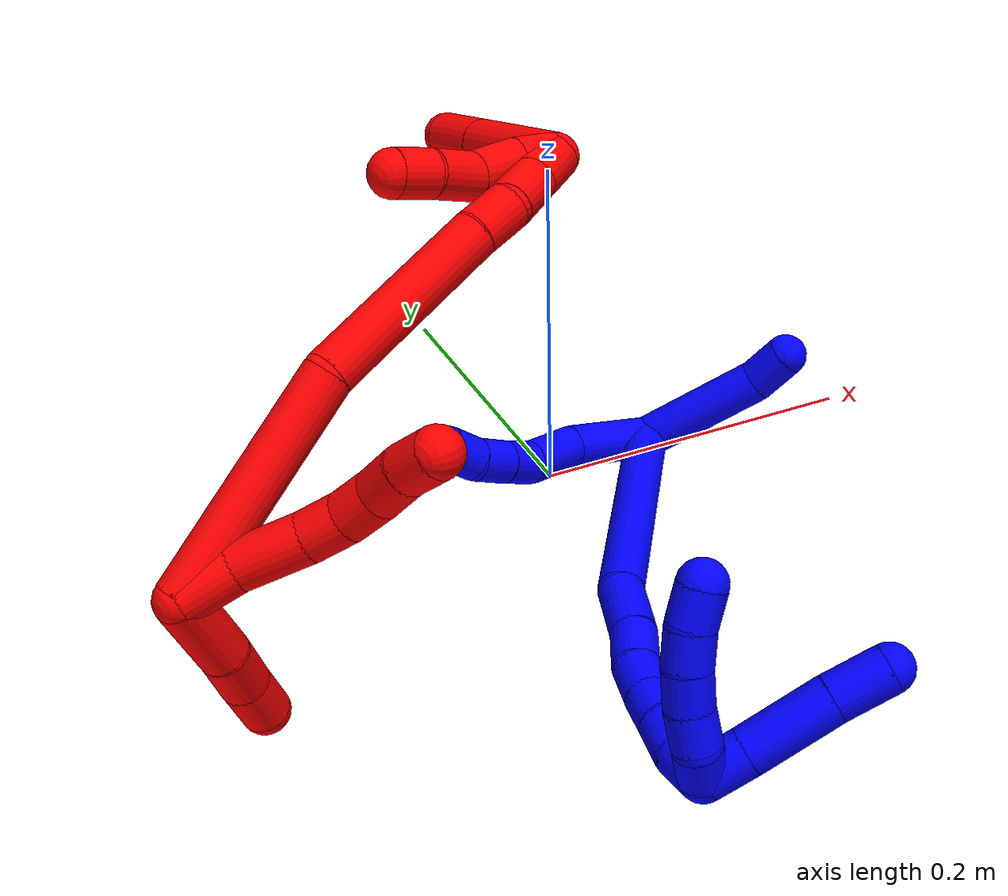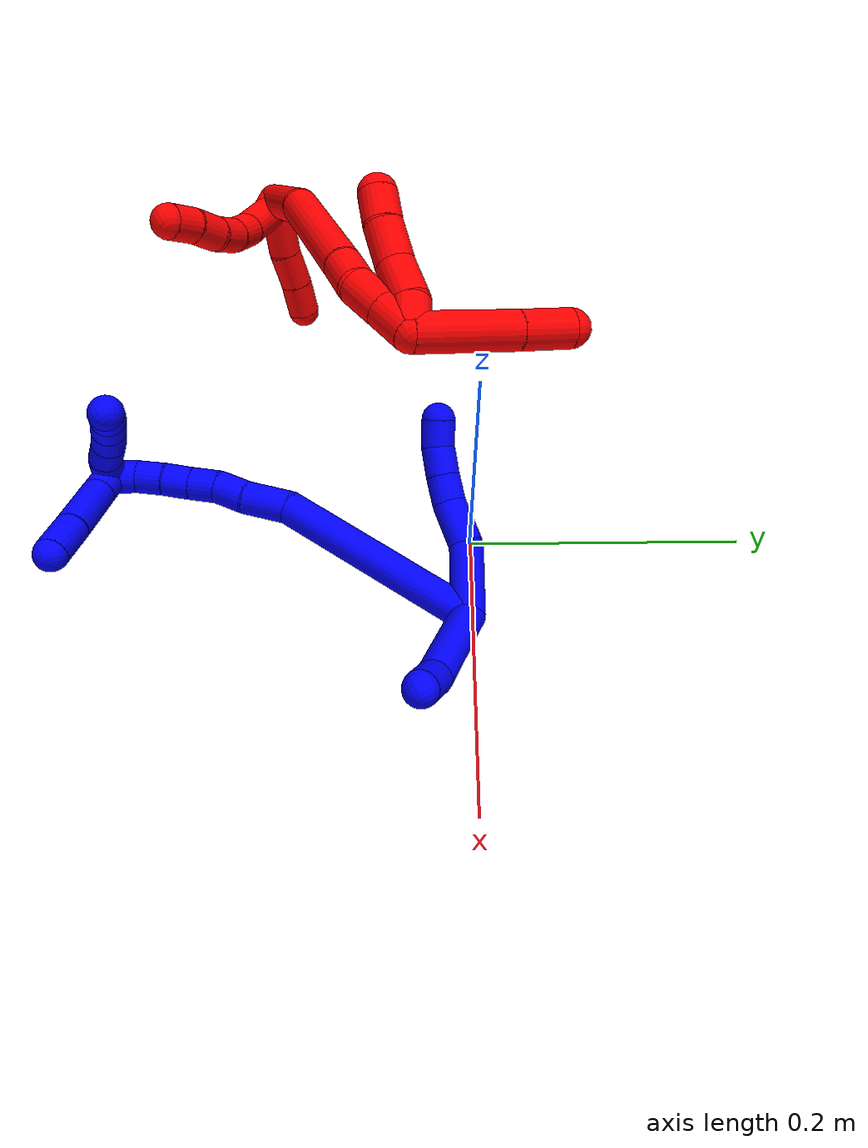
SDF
<sdf version="1.7">
 <world name="default">
  <plugin name="TubeGeneratorPlugin" filename="libtube_generator_plugin.so"/>
  <model name="photoneo_s_sensor">
   <static>1</static>
   <pose>0 0 2 1.57079 1.57079 3.14159</pose>
   <link name="link">
    <inertial><mass>0.1</mass></inertial>
    <sensor name="sensor" type="depth">
     <update_rate>30</update_rate>
     <camera>
      <horizontal_fov>1.22</horizontal_fov>
      <image><width>1920</width><height>1200</height><format>B8G8R8</format></image>
      <clip><near>0.1</near><far>4</far></clip>
      <depth_camera><output>points</output></depth_camera>
     </camera>
     <plugin name="camera_plugin" filename="libgazebo_ros_depth_camera.so">
      <baseline>0.2</baseline>
      <alwaysOn>1</alwaysOn>
      <updateRate>0.0</updateRate>
      <cameraName>camera_ir</cameraName>
      <imageTopicName>/camera/color/image_raw</imageTopicName>
      <cameraInfoTopicName>/camera/color/camera_info</cameraInfoTopicName>
      <depthImageTopicName>/camera/depth/image_raw</depthImageTopicName>
      <depthImageCameraInfoTopicName>/camera/depth/camera_info</depthImageCameraInfoTopicName>
      <pointCloudTopicName>/camera/depth/points</pointCloudTopicName>
      <frameName>fr_optical</frameName>
      <pointCloudCutoff>0.1</pointCloudCutoff>
      <pointCloudCutoffMax>2.0</pointCloudCutoffMax>
      <distortionK1>0</distortionK1>
      <distortionK2>0</distortionK2>
      <distortionK3>0</distortionK3>
      <distortionT1>0</distortionT1>
      <distortionT2>0</distortionT2>
      <CxPrime>0</CxPrime>
      <Cx>0</Cx>
      <Cy>0</Cy>
      <focalLength>0</focalLength>
      <hackBaseline>0</hackBaseline>
     </plugin>
    </sensor>
   </link>
  </model>
  <gravity>0 0 -9.8</gravity>
  <magnetic_field>6e-06 2.3e-05 -4.2e-05</magnetic_field>
  <atmosphere type="adiabatic"/>
  <physics name="default_physics" default="0" type="ode">
   <max_step_size>0.003</max_step_size>
   <real_time_factor>1</real_time_factor>
   <real_time_update_rate>1000</real_time_update_rate>
   <max_contacts>10000</max_contacts>
   <ode>
    <solver>
     <type>quick</type>
     <iters>100</iters>
     <sor>1.3</sor>
     <use_dynamic_moi_rescaling>0</use_dynamic_moi_rescaling>
    </solver>
    <constraints>
     <contact_max_correcting_vel>0</contact_max_correcting_vel>
     <contact_surface_layer>0.001</contact_surface_layer>
     <cfm>0</cfm>
     <erp>0.2</erp>
    </constraints>
   </ode>
  </physics>
  <scene><ambient>0.4 0.4 0.4 1</ambient><background>0.7 0.7 0.7 1</background><shadows>0</shadows></scene>
  <audio><device>default</device></audio>
  <spherical_coordinates>
   <surface_model>EARTH_WGS84</surface_model>
   <latitude_deg>0</latitude_deg>
   <longitude_deg>0</longitude_deg>
   <elevation>0</elevation>
   <heading_deg>0</heading_deg>
  </spherical_coordinates>
  <model name="bin">
   <static>1</static>
   <link name="bottom">
    <collision name="collision-bottom">
     <pose>0 0 -0.01 0 -0 0</pose>
     <geometry><box><size>0.8 0.6 0.02</size></box></geometry>
     <surface>
      <friction><ode><mu>100</mu><mu2>100</mu2></ode></friction>
      <contact><collide_bitmask>65535</collide_bitmask></contact>
     </surface>
    </collision>
   </link>
   <link name="west_wall">
    <collision name="collision-west_wall">
     <pose>-0.41 0 0.1 0 -0 0</pose>
     <geometry><box><size>0.02 0.6 0.2</size></box></geometry>
     <surface>
      <friction><ode><mu>100</mu><mu2>100</mu2></ode></friction>
      <contact><collide_bitmask>65535</collide_bitmask></contact>
     </surface>
    </collision>
   </link>
   <link name="east_wall">
    <collision name="collision-east_wall">
     <pose>0.41 0 0.1 0 -0 0</pose>
     <geometry><box><size>0.02 0.6 0.2</size></box></geometry>
     <surface>
      <friction><ode><mu>100</mu><mu2>100</mu2></ode></friction>
      <contact><collide_bitmask>65535</collide_bitmask></contact>
     </surface>
    </collision>
   </link>
   <link name="south_wall">
    <collision name="collision-south_wall">
     <pose>0 -0.31 0.1 0 -0 0</pose>
     <geometry><box><size>0.8 0.02 0.2</size></box></geometry>
     <surface>
      <friction><ode><mu>100</mu><mu2>100</mu2></ode></friction>
      <contact><collide_bitmask>65535</collide_bitmask></contact>
     </surface>
    </collision>
   </link>
   <link name="north_wall">
    <collision name="collision-north_wall">
     <pose>0 0.31 0.1 0 -0 0</pose>
     <geometry><box><size>0.8 0.02 0.2</size></box></geometry>
     <surface>
      <friction><ode><mu>100</mu><mu2>100</mu2></ode></friction>
      <contact><collide_bitmask>65535</collide_bitmask></contact>
     </surface>
    </collision>
   </link>
  </model>
  <model name="1">
   <static>0</static>
   <link name="1">
    <collision name="collision-cylinder-e_1_2_8">
     <pose>0.000125 0.010987 0.023472 -0.437793 0.004832 -0.001075</pose>
     <geometry><cylinder><radius>0.0125</radius><length>0.051834</length></cylinder></geometry>
     <surface>
      <friction><ode><mu>1.16</mu><mu2>1.16</mu2><slip1>0</slip1><slip2>0</slip2></ode></friction>
      <contact><ode><kp>1e+06</kp><kd>1</kd><max_vel>0</max_vel><min_depth>0.001</min_depth></ode></contact>
     </surface>
    </collision>
    <visual name="visual-cylinder-e_1_2_8">
     <pose>0.000125 0.010987 0.023472 -0.437793 0.004832 -0.001075</pose>
     <geometry><cylinder><radius>0.0125</radius><length>0.051834</length></cylinder></geometry>
     <material><ambient>0 0 1 1</ambient></material>
    </visual>
    <collision name="collision-cylinder-e_2_8_9">
     <pose>0.000234 0.023569 0.064226 -0.091996 -0.000962 4.4e-05</pose>
     <geometry><cylinder><radius>0.0125</radius><length>0.03471</length></cylinder></geometry>
     <surface>
      <friction><ode><mu>1.16</mu><mu2>1.16</mu2><slip1>0</slip1><slip2>0</slip2></ode></friction>
      <contact><ode><kp>1e+06</kp><kd>1</kd><max_vel>0</max_vel><min_depth>0.001</min_depth></ode></contact>
     </surface>
    </collision>
    <visual name="visual-cylinder-e_2_8_9">
     <pose>0.000234 0.023569 0.064226 -0.091996 -0.000962 4.4e-05</pose>
     <geometry><cylinder><radius>0.0125</radius><length>0.03471</length></cylinder></geometry>
     <material><ambient>0 0 1 1</ambient></material>
    </visual>
    <collision name="collision-cylinder-e_3_9_10">
     <pose>0.002975 0.027329 0.09143 -0.214977 0.265143 -0.028777</pose>
     <geometry><cylinder><radius>0.0125</radius><length>0.021046</length></cylinder></geometry>
     <surface>
      <friction><ode><mu>1.16</mu><mu2>1.16</mu2><slip1>0</slip1><slip2>0</slip2></ode></friction>
      <contact><ode><kp>1e+06</kp><kd>1</kd><max_vel>0</max_vel><min_depth>0.001</min_depth></ode></contact>
     </surface>
    </collision>
    <visual name="visual-cylinder-e_3_9_10">
     <pose>0.002975 0.027329 0.09143 -0.214977 0.265143 -0.028777</pose>
     <geometry><cylinder><radius>0.0125</radius><length>0.021046</length></cylinder></geometry>
     <material><ambient>0 0 1 1</ambient></material>
    </visual>
    <collision name="collision-cylinder-e_4_10_11">
     <pose>0.008971 0.032314 0.111455 -0.271989 0.299501 -0.041287</pose>
     <geometry><cylinder><radius>0.0125</radius><length>0.021957</length></cylinder></geometry>
     <surface>
      <friction><ode><mu>1.16</mu><mu2>1.16</mu2><slip1>0</slip1><slip2>0</slip2></ode></friction>
      <contact><ode><kp>1e+06</kp><kd>1</kd><max_vel>0</max_vel><min_depth>0.001</min_depth></ode></contact>
     </surface>
    </collision>
    <visual name="visual-cylinder-e_4_10_11">
     <pose>0.008971 0.032314 0.111455 -0.271989 0.299501 -0.041287</pose>
     <geometry><cylinder><radius>0.0125</radius><length>0.021957</length></cylinder></geometry>
     <material><ambient>0 0 1 1</ambient></material>
    </visual>
    <collision name="collision-cylinder-e_5_11_6">
     <pose>0.017023 0.039152 0.129638 -0.46177 0.490015 -0.117418</pose>
     <geometry><cylinder><radius>0.0125</radius><length>0.020453</length></cylinder></geometry>
     <surface>
      <friction><ode><mu>1.16</mu><mu2>1.16</mu2><slip1>0</slip1><slip2>0</slip2></ode></friction>
      <contact><ode><kp>1e+06</kp><kd>1</kd><max_vel>0</max_vel><min_depth>0.001</min_depth></ode></contact>
     </surface>
    </collision>
    <visual name="visual-cylinder-e_5_11_6">
     <pose>0.017023 0.039152 0.129638 -0.46177 0.490015 -0.117418</pose>
     <geometry><cylinder><radius>0.0125</radius><length>0.020453</length></cylinder></geometry>
     <material><ambient>0 0 1 1</ambient></material>
    </visual>
    <collision name="collision-cylinder-e_1_2_12">
     <pose>0.023324 -0.022717 -0.018862 2.26373 0.668569 1.27388</pose>
     <geometry><cylinder><radius>0.0125</radius><length>0.075256</length></cylinder></geometry>
     <surface>
      <friction><ode><mu>1.16</mu><mu2>1.16</mu2><slip1>0</slip1><slip2>0</slip2></ode></friction>
      <contact><ode><kp>1e+06</kp><kd>1</kd><max_vel>0</max_vel><min_depth>0.001</min_depth></ode></contact>
     </surface>
    </collision>
    <visual name="visual-cylinder-e_1_2_12">
     <pose>0.023324 -0.022717 -0.018862 2.26373 0.668569 1.27388</pose>
     <geometry><cylinder><radius>0.0125</radius><length>0.075256</length></cylinder></geometry>
     <material><ambient>0 0 1 1</ambient></material>
    </visual>
    <collision name="collision-cylinder-e_2_12_5">
     <pose>0.056795 -0.051713 -0.040995 2.05119 0.961629 1.42061</pose>
     <geometry><cylinder><radius>0.0125</radius><length>0.024744</length></cylinder></geometry>
     <surface>
      <friction><ode><mu>1.16</mu><mu2>1.16</mu2><slip1>0</slip1><slip2>0</slip2></ode></friction>
      <contact><ode><kp>1e+06</kp><kd>1</kd><max_vel>0</max_vel><min_depth>0.001</min_depth></ode></contact>
     </surface>
    </collision>
    <visual name="visual-cylinder-e_2_12_5">
     <pose>0.056795 -0.051713 -0.040995 2.05119 0.961629 1.42061</pose>
     <geometry><cylinder><radius>0.0125</radius><length>0.024744</length></cylinder></geometry>
     <material><ambient>0 0 1 1</ambient></material>
    </visual>
    <collision name="collision-cylinder-e_1_2_13">
     <pose>-0.004886 -0.041023 0.066866 0.550294 -0.0622 -0.017565</pose>
     <geometry><cylinder><radius>0.0125</radius><length>0.157198</length></cylinder></geometry>
     <surface>
      <friction><ode><mu>1.16</mu><mu2>1.16</mu2><slip1>0</slip1><slip2>0</slip2></ode></friction>
      <contact><ode><kp>1e+06</kp><kd>1</kd><max_vel>0</max_vel><min_depth>0.001</min_depth></ode></contact>
     </surface>
    </collision>
    <visual name="visual-cylinder-e_1_2_13">
     <pose>-0.004886 -0.041023 0.066866 0.550294 -0.0622 -0.017565</pose>
     <geometry><cylinder><radius>0.0125</radius><length>0.157198</length></cylinder></geometry>
     <material><ambient>0 0 1 1</ambient></material>
    </visual>
    <collision name="collision-cylinder-e_2_13_14">
     <pose>-0.011401 -0.094922 0.144976 0.85295 -0.09505 -0.043213</pose>
     <geometry><cylinder><radius>0.0125</radius><length>0.034346</length></cylinder></geometry>
     <surface>
      <friction><ode><mu>1.16</mu><mu2>1.16</mu2><slip1>0</slip1><slip2>0</slip2></ode></friction>
      <contact><ode><kp>1e+06</kp><kd>1</kd><max_vel>0</max_vel><min_depth>0.001</min_depth></ode></contact>
     </surface>
    </collision>
    <visual name="visual-cylinder-e_2_13_14">
     <pose>-0.011401 -0.094922 0.144976 0.85295 -0.09505 -0.043213</pose>
     <geometry><cylinder><radius>0.0125</radius><length>0.034346</length></cylinder></geometry>
     <material><ambient>0 0 1 1</ambient></material>
    </visual>
    <collision name="collision-cylinder-e_3_14_15">
     <pose>-0.014623 -0.115463 0.165339 0.698986 -0.132848 -0.048479</pose>
     <geometry><cylinder><radius>0.0125</radius><length>0.024033</length></cylinder></geometry>
     <surface>
      <friction><ode><mu>1.16</mu><mu2>1.16</mu2><slip1>0</slip1><slip2>0</slip2></ode></friction>
      <contact><ode><kp>1e+06</kp><kd>1</kd><max_vel>0</max_vel><min_depth>0.001</min_depth></ode></contact>
     </surface>
    </collision>
    <visual name="visual-cylinder-e_3_14_15">
     <pose>-0.014623 -0.115463 0.165339 0.698986 -0.132848 -0.048479</pose>
     <geometry><cylinder><radius>0.0125</radius><length>0.024033</length></cylinder></geometry>
     <material><ambient>0 0 1 1</ambient></material>
    </visual>
    <collision name="collision-cylinder-e_4_15_16">
     <pose>-0.017354 -0.131892 0.180666 0.95443 -0.105654 -0.054668</pose>
     <geometry><cylinder><radius>0.0125</radius><length>0.021606</length></cylinder></geometry>
     <surface>
      <friction><ode><mu>1.16</mu><mu2>1.16</mu2><slip1>0</slip1><slip2>0</slip2></ode></friction>
      <contact><ode><kp>1e+06</kp><kd>1</kd><max_vel>0</max_vel><min_depth>0.001</min_depth></ode></contact>
     </surface>
    </collision>
    <visual name="visual-cylinder-e_4_15_16">
     <pose>-0.017354 -0.131892 0.180666 0.95443 -0.105654 -0.054668</pose>
     <geometry><cylinder><radius>0.0125</radius><length>0.021606</length></cylinder></geometry>
     <material><ambient>0 0 1 1</ambient></material>
    </visual>
    <collision name="collision-cylinder-e_5_16_17">
     <pose>-0.01825 -0.149249 0.192808 0.966516 0.023314 0.012235</pose>
     <geometry><cylinder><radius>0.0125</radius><length>0.020885</length></cylinder></geometry>
     <surface>
      <friction><ode><mu>1.16</mu><mu2>1.16</mu2><slip1>0</slip1><slip2>0</slip2></ode></friction>
      <contact><ode><kp>1e+06</kp><kd>1</kd><max_vel>0</max_vel><min_depth>0.001</min_depth></ode></contact>
     </surface>
    </collision>
    <visual name="visual-cylinder-e_5_16_17">
     <pose>-0.01825 -0.149249 0.192808 0.966516 0.023314 0.012235</pose>
     <geometry><cylinder><radius>0.0125</radius><length>0.020885</length></cylinder></geometry>
     <material><ambient>0 0 1 1</ambient></material>
    </visual>
    <collision name="collision-cylinder-e_6_17_18">
     <pose>-0.01877 -0.166733 0.204543 0.992603 -0.071823 -0.038905</pose>
     <geometry><cylinder><radius>0.0125</radius><length>0.021293</length></cylinder></geometry>
     <surface>
      <friction><ode><mu>1.16</mu><mu2>1.16</mu2><slip1>0</slip1><slip2>0</slip2></ode></friction>
      <contact><ode><kp>1e+06</kp><kd>1</kd><max_vel>0</max_vel><min_depth>0.001</min_depth></ode></contact>
     </surface>
    </collision>
    <visual name="visual-cylinder-e_6_17_18">
     <pose>-0.01877 -0.166733 0.204543 0.992603 -0.071823 -0.038905</pose>
     <geometry><cylinder><radius>0.0125</radius><length>0.021293</length></cylinder></geometry>
     <material><ambient>0 0 1 1</ambient></material>
    </visual>
    <collision name="collision-cylinder-e_7_18_1">
     <pose>-0.018441 -0.185113 0.214257 1.17976 0.10611 0.071065</pose>
     <geometry><cylinder><radius>0.0125</radius><length>0.02064</length></cylinder></geometry>
     <surface>
      <friction><ode><mu>1.16</mu><mu2>1.16</mu2><slip1>0</slip1><slip2>0</slip2></ode></friction>
      <contact><ode><kp>1e+06</kp><kd>1</kd><max_vel>0</max_vel><min_depth>0.001</min_depth></ode></contact>
     </surface>
    </collision>
    <visual name="visual-cylinder-e_7_18_1">
     <pose>-0.018441 -0.185113 0.214257 1.17976 0.10611 0.071065</pose>
     <geometry><cylinder><radius>0.0125</radius><length>0.02064</length></cylinder></geometry>
     <material><ambient>0 0 1 1</ambient></material>
    </visual>
    <collision name="collision-cylinder-e_1_1_19">
     <pose>-0.010878 -0.200167 0.210498 2.51378 0.598961 1.52069</pose>
     <geometry><cylinder><radius>0.0125</radius><length>0.022951</length></cylinder></geometry>
     <surface>
      <friction><ode><mu>1.16</mu><mu2>1.16</mu2><slip1>0</slip1><slip2>0</slip2></ode></friction>
      <contact><ode><kp>1e+06</kp><kd>1</kd><max_vel>0</max_vel><min_depth>0.001</min_depth></ode></contact>
     </surface>
    </collision>
    <visual name="visual-cylinder-e_1_1_19">
     <pose>-0.010878 -0.200167 0.210498 2.51378 0.598961 1.52069</pose>
     <geometry><cylinder><radius>0.0125</radius><length>0.022951</length></cylinder></geometry>
     <material><ambient>0 0 1 1</ambient></material>
    </visual>
    <collision name="collision-cylinder-e_2_19_20">
     <pose>0.009399 -0.216591 0.187212 2.53408 0.627974 1.60612</pose>
     <geometry><cylinder><radius>0.0125</radius><length>0.047004</length></cylinder></geometry>
     <surface>
      <friction><ode><mu>1.16</mu><mu2>1.16</mu2><slip1>0</slip1><slip2>0</slip2></ode></friction>
      <contact><ode><kp>1e+06</kp><kd>1</kd><max_vel>0</max_vel><min_depth>0.001</min_depth></ode></contact>
     </surface>
    </collision>
    <visual name="visual-cylinder-e_2_19_20">
     <pose>0.009399 -0.216591 0.187212 2.53408 0.627974 1.60612</pose>
     <geometry><cylinder><radius>0.0125</radius><length>0.047004</length></cylinder></geometry>
     <material><ambient>0 0 1 1</ambient></material>
    </visual>
    <collision name="collision-cylinder-e_3_20_4">
     <pose>0.031454 -0.235224 0.161739 2.47366 0.581172 1.42274</pose>
     <geometry><cylinder><radius>0.0125</radius><length>0.030044</length></cylinder></geometry>
     <surface>
      <friction><ode><mu>1.16</mu><mu2>1.16</mu2><slip1>0</slip1><slip2>0</slip2></ode></friction>
      <contact><ode><kp>1e+06</kp><kd>1</kd><max_vel>0</max_vel><min_depth>0.001</min_depth></ode></contact>
     </surface>
    </collision>
    <visual name="visual-cylinder-e_3_20_4">
     <pose>0.031454 -0.235224 0.161739 2.47366 0.581172 1.42274</pose>
     <geometry><cylinder><radius>0.0125</radius><length>0.030044</length></cylinder></geometry>
     <material><ambient>0 0 1 1</ambient></material>
    </visual>
    <collision name="collision-cylinder-e_1_1_21">
     <pose>-0.007936 -0.192901 0.221087 -0.527457 1.22633 -0.375515</pose>
     <geometry><cylinder><radius>0.0125</radius><length>0.02</length></cylinder></geometry>
     <surface>
      <friction><ode><mu>1.16</mu><mu2>1.16</mu2><slip1>0</slip1><slip2>0</slip2></ode></friction>
      <contact><ode><kp>1e+06</kp><kd>1</kd><max_vel>0</max_vel><min_depth>0.001</min_depth></ode></contact>
     </surface>
    </collision>
    <visual name="visual-cylinder-e_1_1_21">
     <pose>-0.007936 -0.192901 0.221087 -0.527457 1.22633 -0.375515</pose>
     <geometry><cylinder><radius>0.0125</radius><length>0.02</length></cylinder></geometry>
     <material><ambient>0 0 1 1</ambient></material>
    </visual>
    <collision name="collision-cylinder-e_2_21_22">
     <pose>0.010648 -0.187229 0.224338 -1.48711 1.16079 -1.0853</pose>
     <geometry><cylinder><radius>0.0125</radius><length>0.02</length></cylinder></geometry>
     <surface>
      <friction><ode><mu>1.16</mu><mu2>1.16</mu2><slip1>0</slip1><slip2>0</slip2></ode></friction>
      <contact><ode><kp>1e+06</kp><kd>1</kd><max_vel>0</max_vel><min_depth>0.001</min_depth></ode></contact>
     </surface>
    </collision>
    <visual name="visual-cylinder-e_2_21_22">
     <pose>0.010648 -0.187229 0.224338 -1.48711 1.16079 -1.0853</pose>
     <geometry><cylinder><radius>0.0125</radius><length>0.02</length></cylinder></geometry>
     <material><ambient>0 0 1 1</ambient></material>
    </visual>
    <collision name="collision-cylinder-e_3_22_23">
     <pose>0.029448 -0.180569 0.224429 -1.66061 1.29757 -1.38512</pose>
     <geometry><cylinder><radius>0.0125</radius><length>0.02</length></cylinder></geometry>
     <surface>
      <friction><ode><mu>1.16</mu><mu2>1.16</mu2><slip1>0</slip1><slip2>0</slip2></ode></friction>
      <contact><ode><kp>1e+06</kp><kd>1</kd><max_vel>0</max_vel><min_depth>0.001</min_depth></ode></contact>
     </surface>
    </collision>
    <visual name="visual-cylinder-e_3_22_23">
     <pose>0.029448 -0.180569 0.224429 -1.66061 1.29757 -1.38512</pose>
     <geometry><cylinder><radius>0.0125</radius><length>0.02</length></cylinder></geometry>
     <material><ambient>0 0 1 1</ambient></material>
    </visual>
    <collision name="collision-cylinder-e_4_23_24">
     <pose>0.048778 -0.175884 0.222802 -2.17697 1.32527 -1.95969</pose>
     <geometry><cylinder><radius>0.0125</radius><length>0.02</length></cylinder></geometry>
     <surface>
      <friction><ode><mu>1.16</mu><mu2>1.16</mu2><slip1>0</slip1><slip2>0</slip2></ode></friction>
      <contact><ode><kp>1e+06</kp><kd>1</kd><max_vel>0</max_vel><min_depth>0.001</min_depth></ode></contact>
     </surface>
    </collision>
    <visual name="visual-cylinder-e_4_23_24">
     <pose>0.048778 -0.175884 0.222802 -2.17697 1.32527 -1.95969</pose>
     <geometry><cylinder><radius>0.0125</radius><length>0.02</length></cylinder></geometry>
     <material><ambient>0 0 1 1</ambient></material>
    </visual>
    <collision name="collision-cylinder-e_5_24_3">
     <pose>0.067958 -0.172956 0.218375 -2.8448 1.24706 -2.73173</pose>
     <geometry><cylinder><radius>0.0125</radius><length>0.02</length></cylinder></geometry>
     <surface>
      <friction><ode><mu>1.16</mu><mu2>1.16</mu2><slip1>0</slip1><slip2>0</slip2></ode></friction>
      <contact><ode><kp>1e+06</kp><kd>1</kd><max_vel>0</max_vel><min_depth>0.001</min_depth></ode></contact>
     </surface>
    </collision>
    <visual name="visual-cylinder-e_5_24_3">
     <pose>0.067958 -0.172956 0.218375 -2.8448 1.24706 -2.73173</pose>
     <geometry><cylinder><radius>0.0125</radius><length>0.02</length></cylinder></geometry>
     <material><ambient>0 0 1 1</ambient></material>
    </visual>
    <collision name="collision-sphere-3">
     <pose>0.077439 -0.172026 0.215333 0 -0 0</pose>
     <geometry><sphere><radius>0.0125</radius></sphere></geometry>
     <surface>
      <friction><ode><mu>1.16</mu><mu2>1.16</mu2><slip1>0</slip1><slip2>0</slip2></ode></friction>
      <contact><ode><kp>1e+06</kp><kd>1</kd><max_vel>0</max_vel><min_depth>0.001</min_depth></ode></contact>
     </surface>
    </collision>
    <visual name="visual-sphere-3">
     <pose>0.077439 -0.172026 0.215333 0 -0 0</pose>
     <geometry><sphere><radius>0.0125</radius></sphere></geometry>
     <material><ambient>0 0 1 1</ambient></material>
    </visual>
    <collision name="collision-sphere-24">
     <pose>0.058478 -0.173886 0.221417 0 -0 0</pose>
     <geometry><sphere><radius>0.0125</radius></sphere></geometry>
     <surface>
      <friction><ode><mu>1.16</mu><mu2>1.16</mu2><slip1>0</slip1><slip2>0</slip2></ode></friction>
      <contact><ode><kp>1e+06</kp><kd>1</kd><max_vel>0</max_vel><min_depth>0.001</min_depth></ode></contact>
     </surface>
    </collision>
    <visual name="visual-sphere-24">
     <pose>0.058478 -0.173886 0.221417 0 -0 0</pose>
     <geometry><sphere><radius>0.0125</radius></sphere></geometry>
     <material><ambient>0 0 1 1</ambient></material>
    </visual>
    <collision name="collision-sphere-23">
     <pose>0.039078 -0.177881 0.224187 0 -0 0</pose>
     <geometry><sphere><radius>0.0125</radius></sphere></geometry>
     <surface>
      <friction><ode><mu>1.16</mu><mu2>1.16</mu2><slip1>0</slip1><slip2>0</slip2></ode></friction>
      <contact><ode><kp>1e+06</kp><kd>1</kd><max_vel>0</max_vel><min_depth>0.001</min_depth></ode></contact>
     </surface>
    </collision>
    <visual name="visual-sphere-23">
     <pose>0.039078 -0.177881 0.224187 0 -0 0</pose>
     <geometry><sphere><radius>0.0125</radius></sphere></geometry>
     <material><ambient>0 0 1 1</ambient></material>
    </visual>
    <collision name="collision-sphere-22">
     <pose>0.019819 -0.183256 0.224671 0 -0 0</pose>
     <geometry><sphere><radius>0.0125</radius></sphere></geometry>
     <surface>
      <friction><ode><mu>1.16</mu><mu2>1.16</mu2><slip1>0</slip1><slip2>0</slip2></ode></friction>
      <contact><ode><kp>1e+06</kp><kd>1</kd><max_vel>0</max_vel><min_depth>0.001</min_depth></ode></contact>
     </surface>
    </collision>
    <visual name="visual-sphere-22">
     <pose>0.019819 -0.183256 0.224671 0 -0 0</pose>
     <geometry><sphere><radius>0.0125</radius></sphere></geometry>
     <material><ambient>0 0 1 1</ambient></material>
    </visual>
    <collision name="collision-sphere-21">
     <pose>0.001477 -0.191201 0.224005 0 -0 0</pose>
     <geometry><sphere><radius>0.0125</radius></sphere></geometry>
     <surface>
      <friction><ode><mu>1.16</mu><mu2>1.16</mu2><slip1>0</slip1><slip2>0</slip2></ode></friction>
      <contact><ode><kp>1e+06</kp><kd>1</kd><max_vel>0</max_vel><min_depth>0.001</min_depth></ode></contact>
     </surface>
    </collision>
    <visual name="visual-sphere-21">
     <pose>0.001477 -0.191201 0.224005 0 -0 0</pose>
     <geometry><sphere><radius>0.0125</radius></sphere></geometry>
     <material><ambient>0 0 1 1</ambient></material>
    </visual>
    <collision name="collision-sphere-4">
     <pose>0.039701 -0.243 0.151881 0 -0 0</pose>
     <geometry><sphere><radius>0.0125</radius></sphere></geometry>
     <surface>
      <friction><ode><mu>1.16</mu><mu2>1.16</mu2><slip1>0</slip1><slip2>0</slip2></ode></friction>
      <contact><ode><kp>1e+06</kp><kd>1</kd><max_vel>0</max_vel><min_depth>0.001</min_depth></ode></contact>
     </surface>
    </collision>
    <visual name="visual-sphere-4">
     <pose>0.039701 -0.243 0.151881 0 -0 0</pose>
     <geometry><sphere><radius>0.0125</radius></sphere></geometry>
     <material><ambient>0 0 1 1</ambient></material>
    </visual>
    <collision name="collision-sphere-20">
     <pose>0.023207 -0.227447 0.171596 0 -0 0</pose>
     <geometry><sphere><radius>0.0125</radius></sphere></geometry>
     <surface>
      <friction><ode><mu>1.16</mu><mu2>1.16</mu2><slip1>0</slip1><slip2>0</slip2></ode></friction>
      <contact><ode><kp>1e+06</kp><kd>1</kd><max_vel>0</max_vel><min_depth>0.001</min_depth></ode></contact>
     </surface>
    </collision>
    <visual name="visual-sphere-20">
     <pose>0.023207 -0.227447 0.171596 0 -0 0</pose>
     <geometry><sphere><radius>0.0125</radius></sphere></geometry>
     <material><ambient>0 0 1 1</ambient></material>
    </visual>
    <collision name="collision-sphere-6">
     <pose>0.021836 0.043172 0.137716 0 -0 0</pose>
     <geometry><sphere><radius>0.0125</radius></sphere></geometry>
     <surface>
      <friction><ode><mu>1.16</mu><mu2>1.16</mu2><slip1>0</slip1><slip2>0</slip2></ode></friction>
      <contact><ode><kp>1e+06</kp><kd>1</kd><max_vel>0</max_vel><min_depth>0.001</min_depth></ode></contact>
     </surface>
    </collision>
    <visual name="visual-sphere-6">
     <pose>0.021836 0.043172 0.137716 0 -0 0</pose>
     <geometry><sphere><radius>0.0125</radius></sphere></geometry>
     <material><ambient>0 0 1 1</ambient></material>
    </visual>
    <collision name="collision-sphere-11">
     <pose>0.01221 0.035132 0.121559 0 -0 0</pose>
     <geometry><sphere><radius>0.0125</radius></sphere></geometry>
     <surface>
      <friction><ode><mu>1.16</mu><mu2>1.16</mu2><slip1>0</slip1><slip2>0</slip2></ode></friction>
      <contact><ode><kp>1e+06</kp><kd>1</kd><max_vel>0</max_vel><min_depth>0.001</min_depth></ode></contact>
     </surface>
    </collision>
    <visual name="visual-sphere-11">
     <pose>0.01221 0.035132 0.121559 0 -0 0</pose>
     <geometry><sphere><radius>0.0125</radius></sphere></geometry>
     <material><ambient>0 0 1 1</ambient></material>
    </visual>
    <collision name="collision-sphere-10">
     <pose>0.005732 0.029496 0.101351 0 -0 0</pose>
     <geometry><sphere><radius>0.0125</radius></sphere></geometry>
     <surface>
      <friction><ode><mu>1.16</mu><mu2>1.16</mu2><slip1>0</slip1><slip2>0</slip2></ode></friction>
      <contact><ode><kp>1e+06</kp><kd>1</kd><max_vel>0</max_vel><min_depth>0.001</min_depth></ode></contact>
     </surface>
    </collision>
    <visual name="visual-sphere-10">
     <pose>0.005732 0.029496 0.101351 0 -0 0</pose>
     <geometry><sphere><radius>0.0125</radius></sphere></geometry>
     <material><ambient>0 0 1 1</ambient></material>
    </visual>
    <collision name="collision-sphere-9">
     <pose>0.000217 0.025163 0.081508 0 -0 0</pose>
     <geometry><sphere><radius>0.0125</radius></sphere></geometry>
     <surface>
      <friction><ode><mu>1.16</mu><mu2>1.16</mu2><slip1>0</slip1><slip2>0</slip2></ode></friction>
      <contact><ode><kp>1e+06</kp><kd>1</kd><max_vel>0</max_vel><min_depth>0.001</min_depth></ode></contact>
     </surface>
    </collision>
    <visual name="visual-sphere-9">
     <pose>0.000217 0.025163 0.081508 0 -0 0</pose>
     <geometry><sphere><radius>0.0125</radius></sphere></geometry>
     <material><ambient>0 0 1 1</ambient></material>
    </visual>
    <collision name="collision-sphere-2">
     <geometry><sphere><radius>0.0125</radius></sphere></geometry>
     <surface>
      <friction><ode><mu>1.16</mu><mu2>1.16</mu2><slip1>0</slip1><slip2>0</slip2></ode></friction>
      <contact><ode><kp>1e+06</kp><kd>1</kd><max_vel>0</max_vel><min_depth>0.001</min_depth></ode></contact>
     </surface>
    </collision>
    <visual name="visual-sphere-2">
     <geometry><sphere><radius>0.0125</radius></sphere></geometry>
     <material><ambient>0 0 1 1</ambient></material>
    </visual>
    <collision name="collision-sphere-19">
     <pose>-0.004409 -0.205735 0.202827 0 -0 0</pose>
     <geometry><sphere><radius>0.0125</radius></sphere></geometry>
     <surface>
      <friction><ode><mu>1.16</mu><mu2>1.16</mu2><slip1>0</slip1><slip2>0</slip2></ode></friction>
      <contact><ode><kp>1e+06</kp><kd>1</kd><max_vel>0</max_vel><min_depth>0.001</min_depth></ode></contact>
     </surface>
    </collision>
    <visual name="visual-sphere-19">
     <pose>-0.004409 -0.205735 0.202827 0 -0 0</pose>
     <geometry><sphere><radius>0.0125</radius></sphere></geometry>
     <material><ambient>0 0 1 1</ambient></material>
    </visual>
    <collision name="collision-sphere-8">
     <pose>0.00025 0.021974 0.046945 0 -0 0</pose>
     <geometry><sphere><radius>0.0125</radius></sphere></geometry>
     <surface>
      <friction><ode><mu>1.16</mu><mu2>1.16</mu2><slip1>0</slip1><slip2>0</slip2></ode></friction>
      <contact><ode><kp>1e+06</kp><kd>1</kd><max_vel>0</max_vel><min_depth>0.001</min_depth></ode></contact>
     </surface>
    </collision>
    <visual name="visual-sphere-8">
     <pose>0.00025 0.021974 0.046945 0 -0 0</pose>
     <geometry><sphere><radius>0.0125</radius></sphere></geometry>
     <material><ambient>0 0 1 1</ambient></material>
    </visual>
    <collision name="collision-sphere-12">
     <pose>0.046648 -0.045435 -0.037723 0 -0 0</pose>
     <geometry><sphere><radius>0.0125</radius></sphere></geometry>
     <surface>
      <friction><ode><mu>1.16</mu><mu2>1.16</mu2><slip1>0</slip1><slip2>0</slip2></ode></friction>
      <contact><ode><kp>1e+06</kp><kd>1</kd><max_vel>0</max_vel><min_depth>0.001</min_depth></ode></contact>
     </surface>
    </collision>
    <visual name="visual-sphere-12">
     <pose>0.046648 -0.045435 -0.037723 0 -0 0</pose>
     <geometry><sphere><radius>0.0125</radius></sphere></geometry>
     <material><ambient>0 0 1 1</ambient></material>
    </visual>
    <collision name="collision-sphere-5">
     <pose>0.066942 -0.05799 -0.044266 0 -0 0</pose>
     <geometry><sphere><radius>0.0125</radius></sphere></geometry>
     <surface>
      <friction><ode><mu>1.16</mu><mu2>1.16</mu2><slip1>0</slip1><slip2>0</slip2></ode></friction>
      <contact><ode><kp>1e+06</kp><kd>1</kd><max_vel>0</max_vel><min_depth>0.001</min_depth></ode></contact>
     </surface>
    </collision>
    <visual name="visual-sphere-5">
     <pose>0.066942 -0.05799 -0.044266 0 -0 0</pose>
     <geometry><sphere><radius>0.0125</radius></sphere></geometry>
     <material><ambient>0 0 1 1</ambient></material>
    </visual>
    <collision name="collision-sphere-13">
     <pose>-0.009771 -0.082046 0.133732 0 -0 0</pose>
     <geometry><sphere><radius>0.0125</radius></sphere></geometry>
     <surface>
      <friction><ode><mu>1.16</mu><mu2>1.16</mu2><slip1>0</slip1><slip2>0</slip2></ode></friction>
      <contact><ode><kp>1e+06</kp><kd>1</kd><max_vel>0</max_vel><min_depth>0.001</min_depth></ode></contact>
     </surface>
    </collision>
    <visual name="visual-sphere-13">
     <pose>-0.009771 -0.082046 0.133732 0 -0 0</pose>
     <geometry><sphere><radius>0.0125</radius></sphere></geometry>
     <material><ambient>0 0 1 1</ambient></material>
    </visual>
    <collision name="collision-sphere-14">
     <pose>-0.013031 -0.107799 0.156221 0 -0 0</pose>
     <geometry><sphere><radius>0.0125</radius></sphere></geometry>
     <surface>
      <friction><ode><mu>1.16</mu><mu2>1.16</mu2><slip1>0</slip1><slip2>0</slip2></ode></friction>
      <contact><ode><kp>1e+06</kp><kd>1</kd><max_vel>0</max_vel><min_depth>0.001</min_depth></ode></contact>
     </surface>
    </collision>
    <visual name="visual-sphere-14">
     <pose>-0.013031 -0.107799 0.156221 0 -0 0</pose>
     <geometry><sphere><radius>0.0125</radius></sphere></geometry>
     <material><ambient>0 0 1 1</ambient></material>
    </visual>
    <collision name="collision-sphere-15">
     <pose>-0.016214 -0.123126 0.174456 0 -0 0</pose>
     <geometry><sphere><radius>0.0125</radius></sphere></geometry>
     <surface>
      <friction><ode><mu>1.16</mu><mu2>1.16</mu2><slip1>0</slip1><slip2>0</slip2></ode></friction>
      <contact><ode><kp>1e+06</kp><kd>1</kd><max_vel>0</max_vel><min_depth>0.001</min_depth></ode></contact>
     </surface>
    </collision>
    <visual name="visual-sphere-15">
     <pose>-0.016214 -0.123126 0.174456 0 -0 0</pose>
     <geometry><sphere><radius>0.0125</radius></sphere></geometry>
     <material><ambient>0 0 1 1</ambient></material>
    </visual>
    <collision name="collision-sphere-16">
     <pose>-0.018493 -0.140658 0.186876 0 -0 0</pose>
     <geometry><sphere><radius>0.0125</radius></sphere></geometry>
     <surface>
      <friction><ode><mu>1.16</mu><mu2>1.16</mu2><slip1>0</slip1><slip2>0</slip2></ode></friction>
      <contact><ode><kp>1e+06</kp><kd>1</kd><max_vel>0</max_vel><min_depth>0.001</min_depth></ode></contact>
     </surface>
    </collision>
    <visual name="visual-sphere-16">
     <pose>-0.018493 -0.140658 0.186876 0 -0 0</pose>
     <geometry><sphere><radius>0.0125</radius></sphere></geometry>
     <material><ambient>0 0 1 1</ambient></material>
    </visual>
    <collision name="collision-sphere-17">
     <pose>-0.018006 -0.15784 0.198739 0 -0 0</pose>
     <geometry><sphere><radius>0.0125</radius></sphere></geometry>
     <surface>
      <friction><ode><mu>1.16</mu><mu2>1.16</mu2><slip1>0</slip1><slip2>0</slip2></ode></friction>
      <contact><ode><kp>1e+06</kp><kd>1</kd><max_vel>0</max_vel><min_depth>0.001</min_depth></ode></contact>
     </surface>
    </collision>
    <visual name="visual-sphere-17">
     <pose>-0.018006 -0.15784 0.198739 0 -0 0</pose>
     <geometry><sphere><radius>0.0125</radius></sphere></geometry>
     <material><ambient>0 0 1 1</ambient></material>
    </visual>
    <collision name="collision-sphere-18">
     <pose>-0.019534 -0.175626 0.210346 0 -0 0</pose>
     <geometry><sphere><radius>0.0125</radius></sphere></geometry>
     <surface>
      <friction><ode><mu>1.16</mu><mu2>1.16</mu2><slip1>0</slip1><slip2>0</slip2></ode></friction>
      <contact><ode><kp>1e+06</kp><kd>1</kd><max_vel>0</max_vel><min_depth>0.001</min_depth></ode></contact>
     </surface>
    </collision>
    <visual name="visual-sphere-18">
     <pose>-0.019534 -0.175626 0.210346 0 -0 0</pose>
     <geometry><sphere><radius>0.0125</radius></sphere></geometry>
     <material><ambient>0 0 1 1</ambient></material>
    </visual>
    <collision name="collision-sphere-1">
     <pose>-0.017348 -0.1946 0.218169 0 -0 0</pose>
     <geometry><sphere><radius>0.0125</radius></sphere></geometry>
     <surface>
      <friction><ode><mu>1.16</mu><mu2>1.16</mu2><slip1>0</slip1><slip2>0</slip2></ode></friction>
      <contact><ode><kp>1e+06</kp><kd>1</kd><max_vel>0</max_vel><min_depth>0.001</min_depth></ode></contact>
     </surface>
    </collision>
    <visual name="visual-sphere-1">
     <pose>-0.017348 -0.1946 0.218169 0 -0 0</pose>
     <geometry><sphere><radius>0.0125</radius></sphere></geometry>
     <material><ambient>0 0 1 1</ambient></material>
    </visual>
    <inertial>
     <pose>0.006468 -0.08716 0.113224 0 -0 0</pose>
     <mass>0.75</mass>
     <inertia>
      <ixx>0.000427</ixx>
      <ixy>0</ixy>
      <ixz>0</ixz>
      <iyy>0.000352</iyy>
      <iyz>0</iyz>
      <izz>0.000202</izz>
     </inertia>
    </inertial>
   </link>
   <pose>0.063427 -0.003438 0.011499 0.388267 -1.41207 0.050061</pose>
  </model>
  <model name="2">
   <static>0</static>
   <link name="2">
    <collision name="collision-cylinder-e_1_2_8">
     <pose>0.008466 -0.00306 -0.011084 2.87226 0.634687 2.3591</pose>
     <geometry><cylinder><radius>0.0125</radius><length>0.028558</length></cylinder></geometry>
     <surface>
      <friction><ode><mu>1.16</mu><mu2>1.16</mu2><slip1>0</slip1><slip2>0</slip2></ode></friction>
      <contact><ode><kp>1e+06</kp><kd>1</kd><max_vel>0</max_vel><min_depth>0.001</min_depth></ode></contact>
     </surface>
    </collision>
    <visual name="visual-cylinder-e_1_2_8">
     <pose>0.008466 -0.00306 -0.011084 2.87226 0.634687 2.3591</pose>
     <geometry><cylinder><radius>0.0125</radius><length>0.028558</length></cylinder></geometry>
     <material><ambient>1 0 0 1</ambient></material>
    </visual>
    <collision name="collision-cylinder-e_2_8_9">
     <pose>0.028714 -0.013458 -0.033641 2.57252 0.713131 1.81031</pose>
     <geometry><cylinder><radius>0.0125</radius><length>0.036018</length></cylinder></geometry>
     <surface>
      <friction><ode><mu>1.16</mu><mu2>1.16</mu2><slip1>0</slip1><slip2>0</slip2></ode></friction>
      <contact><ode><kp>1e+06</kp><kd>1</kd><max_vel>0</max_vel><min_depth>0.001</min_depth></ode></contact>
     </surface>
    </collision>
    <visual name="visual-cylinder-e_2_8_9">
     <pose>0.028714 -0.013458 -0.033641 2.57252 0.713131 1.81031</pose>
     <geometry><cylinder><radius>0.0125</radius><length>0.036018</length></cylinder></geometry>
     <material><ambient>1 0 0 1</ambient></material>
    </visual>
    <collision name="collision-cylinder-e_3_9_10">
     <pose>0.048427 -0.02454 -0.050687 2.55013 0.868503 1.97914</pose>
     <geometry><cylinder><radius>0.0125</radius><length>0.020781</length></cylinder></geometry>
     <surface>
      <friction><ode><mu>1.16</mu><mu2>1.16</mu2><slip1>0</slip1><slip2>0</slip2></ode></friction>
      <contact><ode><kp>1e+06</kp><kd>1</kd><max_vel>0</max_vel><min_depth>0.001</min_depth></ode></contact>
     </surface>
    </collision>
    <visual name="visual-cylinder-e_3_9_10">
     <pose>0.048427 -0.02454 -0.050687 2.55013 0.868503 1.97914</pose>
     <geometry><cylinder><radius>0.0125</radius><length>0.020781</length></cylinder></geometry>
     <material><ambient>1 0 0 1</ambient></material>
    </visual>
    <collision name="collision-cylinder-e_4_10_11">
     <pose>0.065874 -0.031363 -0.059723 2.41479 1.11745 2.0486</pose>
     <geometry><cylinder><radius>0.0125</radius><length>0.021169</length></cylinder></geometry>
     <surface>
      <friction><ode><mu>1.16</mu><mu2>1.16</mu2><slip1>0</slip1><slip2>0</slip2></ode></friction>
      <contact><ode><kp>1e+06</kp><kd>1</kd><max_vel>0</max_vel><min_depth>0.001</min_depth></ode></contact>
     </surface>
    </collision>
    <visual name="visual-cylinder-e_4_10_11">
     <pose>0.065874 -0.031363 -0.059723 2.41479 1.11745 2.0486</pose>
     <geometry><cylinder><radius>0.0125</radius><length>0.021169</length></cylinder></geometry>
     <material><ambient>1 0 0 1</ambient></material>
    </visual>
    <collision name="collision-cylinder-e_5_11_12">
     <pose>0.086238 -0.037568 -0.064199 1.88404 1.2768 1.59097</pose>
     <geometry><cylinder><radius>0.0125</radius><length>0.022669</length></cylinder></geometry>
     <surface>
      <friction><ode><mu>1.16</mu><mu2>1.16</mu2><slip1>0</slip1><slip2>0</slip2></ode></friction>
      <contact><ode><kp>1e+06</kp><kd>1</kd><max_vel>0</max_vel><min_depth>0.001</min_depth></ode></contact>
     </surface>
    </collision>
    <visual name="visual-cylinder-e_5_11_12">
     <pose>0.086238 -0.037568 -0.064199 1.88404 1.2768 1.59097</pose>
     <geometry><cylinder><radius>0.0125</radius><length>0.022669</length></cylinder></geometry>
     <material><ambient>1 0 0 1</ambient></material>
    </visual>
    <collision name="collision-cylinder-e_6_12_6">
     <pose>0.106475 -0.044985 -0.066493 1.86088 1.12561 1.40513</pose>
     <geometry><cylinder><radius>0.0125</radius><length>0.020805</length></cylinder></geometry>
     <surface>
      <friction><ode><mu>1.16</mu><mu2>1.16</mu2><slip1>0</slip1><slip2>0</slip2></ode></friction>
      <contact><ode><kp>1e+06</kp><kd>1</kd><max_vel>0</max_vel><min_depth>0.001</min_depth></ode></contact>
     </surface>
    </collision>
    <visual name="visual-cylinder-e_6_12_6">
     <pose>0.106475 -0.044985 -0.066493 1.86088 1.12561 1.40513</pose>
     <geometry><cylinder><radius>0.0125</radius><length>0.020805</length></cylinder></geometry>
     <material><ambient>1 0 0 1</ambient></material>
    </visual>
    <collision name="collision-cylinder-e_1_2_13">
     <pose>-0.017166 -0.009365 -0.010072 2.39252 -0.895343 -1.76961</pose>
     <geometry><cylinder><radius>0.0125</radius><length>0.043993</length></cylinder></geometry>
     <surface>
      <friction><ode><mu>1.16</mu><mu2>1.16</mu2><slip1>0</slip1><slip2>0</slip2></ode></friction>
      <contact><ode><kp>1e+06</kp><kd>1</kd><max_vel>0</max_vel><min_depth>0.001</min_depth></ode></contact>
     </surface>
    </collision>
    <visual name="visual-cylinder-e_1_2_13">
     <pose>-0.017166 -0.009365 -0.010072 2.39252 -0.895343 -1.76961</pose>
     <geometry><cylinder><radius>0.0125</radius><length>0.043993</length></cylinder></geometry>
     <material><ambient>1 0 0 1</ambient></material>
    </visual>
    <collision name="collision-cylinder-e_2_13_14">
     <pose>-0.046694 -0.022829 -0.026637 2.57857 -1.01494 -2.18241</pose>
     <geometry><cylinder><radius>0.0125</radius><length>0.029104</length></cylinder></geometry>
     <surface>
      <friction><ode><mu>1.16</mu><mu2>1.16</mu2><slip1>0</slip1><slip2>0</slip2></ode></friction>
      <contact><ode><kp>1e+06</kp><kd>1</kd><max_vel>0</max_vel><min_depth>0.001</min_depth></ode></contact>
     </surface>
    </collision>
    <visual name="visual-cylinder-e_2_13_14">
     <pose>-0.046694 -0.022829 -0.026637 2.57857 -1.01494 -2.18241</pose>
     <geometry><cylinder><radius>0.0125</radius><length>0.029104</length></cylinder></geometry>
     <material><ambient>1 0 0 1</ambient></material>
    </visual>
    <collision name="collision-cylinder-e_3_14_5">
     <pose>-0.070028 -0.031766 -0.039225 2.47057 -0.95396 -1.95443</pose>
     <geometry><cylinder><radius>0.0125</radius><length>0.026903</length></cylinder></geometry>
     <surface>
      <friction><ode><mu>1.16</mu><mu2>1.16</mu2><slip1>0</slip1><slip2>0</slip2></ode></friction>
      <contact><ode><kp>1e+06</kp><kd>1</kd><max_vel>0</max_vel><min_depth>0.001</min_depth></ode></contact>
     </surface>
    </collision>
    <visual name="visual-cylinder-e_3_14_5">
     <pose>-0.070028 -0.031766 -0.039225 2.47057 -0.95396 -1.95443</pose>
     <geometry><cylinder><radius>0.0125</radius><length>0.026903</length></cylinder></geometry>
     <material><ambient>1 0 0 1</ambient></material>
    </visual>
    <collision name="collision-cylinder-e_1_2_15">
     <pose>0.038932 0.014586 -0.04383 -2.82034 0.700303 -2.30647</pose>
     <geometry><cylinder><radius>0.0125</radius><length>0.120821</length></cylinder></geometry>
     <surface>
      <friction><ode><mu>1.16</mu><mu2>1.16</mu2><slip1>0</slip1><slip2>0</slip2></ode></friction>
      <contact><ode><kp>1e+06</kp><kd>1</kd><max_vel>0</max_vel><min_depth>0.001</min_depth></ode></contact>
     </surface>
    </collision>
    <visual name="visual-cylinder-e_1_2_15">
     <pose>0.038932 0.014586 -0.04383 -2.82034 0.700303 -2.30647</pose>
     <geometry><cylinder><radius>0.0125</radius><length>0.120821</length></cylinder></geometry>
     <material><ambient>1 0 0 1</ambient></material>
    </visual>
    <collision name="collision-cylinder-e_2_15_16">
     <pose>0.098148 0.035934 -0.134046 -2.99682 0.408398 -2.46798</pose>
     <geometry><cylinder><radius>0.0125</radius><length>0.102155</length></cylinder></geometry>
     <surface>
      <friction><ode><mu>1.16</mu><mu2>1.16</mu2><slip1>0</slip1><slip2>0</slip2></ode></friction>
      <contact><ode><kp>1e+06</kp><kd>1</kd><max_vel>0</max_vel><min_depth>0.001</min_depth></ode></contact>
     </surface>
    </collision>
    <visual name="visual-cylinder-e_2_15_16">
     <pose>0.098148 0.035934 -0.134046 -2.99682 0.408398 -2.46798</pose>
     <geometry><cylinder><radius>0.0125</radius><length>0.102155</length></cylinder></geometry>
     <material><ambient>1 0 0 1</ambient></material>
    </visual>
    <collision name="collision-cylinder-e_3_16_17">
     <pose>0.122216 0.044005 -0.192268 -3.03145 0.30759 -2.45826</pose>
     <geometry><cylinder><radius>0.0125</radius><length>0.02499</length></cylinder></geometry>
     <surface>
      <friction><ode><mu>1.16</mu><mu2>1.16</mu2><slip1>0</slip1><slip2>0</slip2></ode></friction>
      <contact><ode><kp>1e+06</kp><kd>1</kd><max_vel>0</max_vel><min_depth>0.001</min_depth></ode></contact>
     </surface>
    </collision>
    <visual name="visual-cylinder-e_3_16_17">
     <pose>0.122216 0.044005 -0.192268 -3.03145 0.30759 -2.45826</pose>
     <geometry><cylinder><radius>0.0125</radius><length>0.02499</length></cylinder></geometry>
     <material><ambient>1 0 0 1</ambient></material>
    </visual>
    <collision name="collision-cylinder-e_4_17_18">
     <pose>0.126584 0.049346 -0.21693 -2.837 0.043464 -0.28135</pose>
     <geometry><cylinder><radius>0.0125</radius><length>0.026913</length></cylinder></geometry>
     <surface>
      <friction><ode><mu>1.16</mu><mu2>1.16</mu2><slip1>0</slip1><slip2>0</slip2></ode></friction>
      <contact><ode><kp>1e+06</kp><kd>1</kd><max_vel>0</max_vel><min_depth>0.001</min_depth></ode></contact>
     </surface>
    </collision>
    <visual name="visual-cylinder-e_4_17_18">
     <pose>0.126584 0.049346 -0.21693 -2.837 0.043464 -0.28135</pose>
     <geometry><cylinder><radius>0.0125</radius><length>0.026913</length></cylinder></geometry>
     <material><ambient>1 0 0 1</ambient></material>
    </visual>
    <collision name="collision-cylinder-e_5_18_1">
     <pose>0.127943 0.057049 -0.241742 -2.84446 0.061696 -0.406643</pose>
     <geometry><cylinder><radius>0.0125</radius><length>0.025121</length></cylinder></geometry>
     <surface>
      <friction><ode><mu>1.16</mu><mu2>1.16</mu2><slip1>0</slip1><slip2>0</slip2></ode></friction>
      <contact><ode><kp>1e+06</kp><kd>1</kd><max_vel>0</max_vel><min_depth>0.001</min_depth></ode></contact>
     </surface>
    </collision>
    <visual name="visual-cylinder-e_5_18_1">
     <pose>0.127943 0.057049 -0.241742 -2.84446 0.061696 -0.406643</pose>
     <geometry><cylinder><radius>0.0125</radius><length>0.025121</length></cylinder></geometry>
     <material><ambient>1 0 0 1</ambient></material>
    </visual>
    <collision name="collision-cylinder-e_1_1_19">
     <pose>0.126815 0.064763 -0.243811 -0.387136 -0.175808 0.034548</pose>
     <geometry><cylinder><radius>0.0125</radius><length>0.021756</length></cylinder></geometry>
     <surface>
      <friction><ode><mu>1.16</mu><mu2>1.16</mu2><slip1>0</slip1><slip2>0</slip2></ode></friction>
      <contact><ode><kp>1e+06</kp><kd>1</kd><max_vel>0</max_vel><min_depth>0.001</min_depth></ode></contact>
     </surface>
    </collision>
    <visual name="visual-cylinder-e_1_1_19">
     <pose>0.126815 0.064763 -0.243811 -0.387136 -0.175808 0.034548</pose>
     <geometry><cylinder><radius>0.0125</radius><length>0.021756</length></cylinder></geometry>
     <material><ambient>1 0 0 1</ambient></material>
    </visual>
    <collision name="collision-cylinder-e_2_19_20">
     <pose>0.123893 0.070022 -0.219285 -0.083041 -0.069422 0.002885</pose>
     <geometry><cylinder><radius>0.0125</radius><length>0.029389</length></cylinder></geometry>
     <surface>
      <friction><ode><mu>1.16</mu><mu2>1.16</mu2><slip1>0</slip1><slip2>0</slip2></ode></friction>
      <contact><ode><kp>1e+06</kp><kd>1</kd><max_vel>0</max_vel><min_depth>0.001</min_depth></ode></contact>
     </surface>
    </collision>
    <visual name="visual-cylinder-e_2_19_20">
     <pose>0.123893 0.070022 -0.219285 -0.083041 -0.069422 0.002885</pose>
     <geometry><cylinder><radius>0.0125</radius><length>0.029389</length></cylinder></geometry>
     <material><ambient>1 0 0 1</ambient></material>
    </visual>
    <collision name="collision-cylinder-e_3_20_21">
     <pose>0.125705 0.074296 -0.191617 -0.230042 0.208054 -0.024123</pose>
     <geometry><cylinder><radius>0.0125</radius><length>0.027416</length></cylinder></geometry>
     <surface>
      <friction><ode><mu>1.16</mu><mu2>1.16</mu2><slip1>0</slip1><slip2>0</slip2></ode></friction>
      <contact><ode><kp>1e+06</kp><kd>1</kd><max_vel>0</max_vel><min_depth>0.001</min_depth></ode></contact>
     </surface>
    </collision>
    <visual name="visual-cylinder-e_3_20_21">
     <pose>0.125705 0.074296 -0.191617 -0.230042 0.208054 -0.024123</pose>
     <geometry><cylinder><radius>0.0125</radius><length>0.027416</length></cylinder></geometry>
     <material><ambient>1 0 0 1</ambient></material>
    </visual>
    <collision name="collision-cylinder-e_4_21_4">
     <pose>0.1293 0.080557 -0.168357 -0.304173 0.071285 -0.01093</pose>
     <geometry><cylinder><radius>0.0125</radius><length>0.021439</length></cylinder></geometry>
     <surface>
      <friction><ode><mu>1.16</mu><mu2>1.16</mu2><slip1>0</slip1><slip2>0</slip2></ode></friction>
      <contact><ode><kp>1e+06</kp><kd>1</kd><max_vel>0</max_vel><min_depth>0.001</min_depth></ode></contact>
     </surface>
    </collision>
    <visual name="visual-cylinder-e_4_21_4">
     <pose>0.1293 0.080557 -0.168357 -0.304173 0.071285 -0.01093</pose>
     <geometry><cylinder><radius>0.0125</radius><length>0.021439</length></cylinder></geometry>
     <material><ambient>1 0 0 1</ambient></material>
    </visual>
    <collision name="collision-cylinder-e_1_1_22">
     <pose>0.109684 0.087001 -0.26128 -1.85058 -0.608067 0.789474</pose>
     <geometry><cylinder><radius>0.0125</radius><length>0.066635</length></cylinder></geometry>
     <surface>
      <friction><ode><mu>1.16</mu><mu2>1.16</mu2><slip1>0</slip1><slip2>0</slip2></ode></friction>
      <contact><ode><kp>1e+06</kp><kd>1</kd><max_vel>0</max_vel><min_depth>0.001</min_depth></ode></contact>
     </surface>
    </collision>
    <visual name="visual-cylinder-e_1_1_22">
     <pose>0.109684 0.087001 -0.26128 -1.85058 -0.608067 0.789474</pose>
     <geometry><cylinder><radius>0.0125</radius><length>0.066635</length></cylinder></geometry>
     <material><ambient>1 0 0 1</ambient></material>
    </visual>
    <collision name="collision-cylinder-e_2_22_3">
     <pose>0.081148 0.12654 -0.272334 -1.82909 -0.606018 0.771267</pose>
     <geometry><cylinder><radius>0.0125</radius><length>0.033365</length></cylinder></geometry>
     <surface>
      <friction><ode><mu>1.16</mu><mu2>1.16</mu2><slip1>0</slip1><slip2>0</slip2></ode></friction>
      <contact><ode><kp>1e+06</kp><kd>1</kd><max_vel>0</max_vel><min_depth>0.001</min_depth></ode></contact>
     </surface>
    </collision>
    <visual name="visual-cylinder-e_2_22_3">
     <pose>0.081148 0.12654 -0.272334 -1.82909 -0.606018 0.771267</pose>
     <geometry><cylinder><radius>0.0125</radius><length>0.033365</length></cylinder></geometry>
     <material><ambient>1 0 0 1</ambient></material>
    </visual>
    <collision name="collision-sphere-3">
     <pose>0.071645 0.139797 -0.275836 0 -0 0</pose>
     <geometry><sphere><radius>0.0125</radius></sphere></geometry>
     <surface>
      <friction><ode><mu>1.16</mu><mu2>1.16</mu2><slip1>0</slip1><slip2>0</slip2></ode></friction>
      <contact><ode><kp>1e+06</kp><kd>1</kd><max_vel>0</max_vel><min_depth>0.001</min_depth></ode></contact>
     </surface>
    </collision>
    <visual name="visual-sphere-3">
     <pose>0.071645 0.139797 -0.275836 0 -0 0</pose>
     <geometry><sphere><radius>0.0125</radius></sphere></geometry>
     <material><ambient>1 0 0 1</ambient></material>
    </visual>
    <collision name="collision-sphere-22">
     <pose>0.09065 0.113283 -0.268831 0 -0 0</pose>
     <geometry><sphere><radius>0.0125</radius></sphere></geometry>
     <surface>
      <friction><ode><mu>1.16</mu><mu2>1.16</mu2><slip1>0</slip1><slip2>0</slip2></ode></friction>
      <contact><ode><kp>1e+06</kp><kd>1</kd><max_vel>0</max_vel><min_depth>0.001</min_depth></ode></contact>
     </surface>
    </collision>
    <visual name="visual-sphere-22">
     <pose>0.09065 0.113283 -0.268831 0 -0 0</pose>
     <geometry><sphere><radius>0.0125</radius></sphere></geometry>
     <material><ambient>1 0 0 1</ambient></material>
    </visual>
    <collision name="collision-sphere-4">
     <pose>0.130063 0.083759 -0.158155 0 -0 0</pose>
     <geometry><sphere><radius>0.0125</radius></sphere></geometry>
     <surface>
      <friction><ode><mu>1.16</mu><mu2>1.16</mu2><slip1>0</slip1><slip2>0</slip2></ode></friction>
      <contact><ode><kp>1e+06</kp><kd>1</kd><max_vel>0</max_vel><min_depth>0.001</min_depth></ode></contact>
     </surface>
    </collision>
    <visual name="visual-sphere-4">
     <pose>0.130063 0.083759 -0.158155 0 -0 0</pose>
     <geometry><sphere><radius>0.0125</radius></sphere></geometry>
     <material><ambient>1 0 0 1</ambient></material>
    </visual>
    <collision name="collision-sphere-21">
     <pose>0.128536 0.077354 -0.178558 0 -0 0</pose>
     <geometry><sphere><radius>0.0125</radius></sphere></geometry>
     <surface>
      <friction><ode><mu>1.16</mu><mu2>1.16</mu2><slip1>0</slip1><slip2>0</slip2></ode></friction>
      <contact><ode><kp>1e+06</kp><kd>1</kd><max_vel>0</max_vel><min_depth>0.001</min_depth></ode></contact>
     </surface>
    </collision>
    <visual name="visual-sphere-21">
     <pose>0.128536 0.077354 -0.178558 0 -0 0</pose>
     <geometry><sphere><radius>0.0125</radius></sphere></geometry>
     <material><ambient>1 0 0 1</ambient></material>
    </visual>
    <collision name="collision-sphere-20">
     <pose>0.122873 0.071238 -0.204676 0 -0 0</pose>
     <geometry><sphere><radius>0.0125</radius></sphere></geometry>
     <surface>
      <friction><ode><mu>1.16</mu><mu2>1.16</mu2><slip1>0</slip1><slip2>0</slip2></ode></friction>
      <contact><ode><kp>1e+06</kp><kd>1</kd><max_vel>0</max_vel><min_depth>0.001</min_depth></ode></contact>
     </surface>
    </collision>
    <visual name="visual-sphere-20">
     <pose>0.122873 0.071238 -0.204676 0 -0 0</pose>
     <geometry><sphere><radius>0.0125</radius></sphere></geometry>
     <material><ambient>1 0 0 1</ambient></material>
    </visual>
    <collision name="collision-sphere-12">
     <pose>0.097086 -0.040693 -0.065211 0 -0 0</pose>
     <geometry><sphere><radius>0.0125</radius></sphere></geometry>
     <surface>
      <friction><ode><mu>1.16</mu><mu2>1.16</mu2><slip1>0</slip1><slip2>0</slip2></ode></friction>
      <contact><ode><kp>1e+06</kp><kd>1</kd><max_vel>0</max_vel><min_depth>0.001</min_depth></ode></contact>
     </surface>
    </collision>
    <visual name="visual-sphere-12">
     <pose>0.097086 -0.040693 -0.065211 0 -0 0</pose>
     <geometry><sphere><radius>0.0125</radius></sphere></geometry>
     <material><ambient>1 0 0 1</ambient></material>
    </visual>
    <collision name="collision-sphere-11">
     <pose>0.07539 -0.034443 -0.063187 0 -0 0</pose>
     <geometry><sphere><radius>0.0125</radius></sphere></geometry>
     <surface>
      <friction><ode><mu>1.16</mu><mu2>1.16</mu2><slip1>0</slip1><slip2>0</slip2></ode></friction>
      <contact><ode><kp>1e+06</kp><kd>1</kd><max_vel>0</max_vel><min_depth>0.001</min_depth></ode></contact>
     </surface>
    </collision>
    <visual name="visual-sphere-11">
     <pose>0.07539 -0.034443 -0.063187 0 -0 0</pose>
     <geometry><sphere><radius>0.0125</radius></sphere></geometry>
     <material><ambient>1 0 0 1</ambient></material>
    </visual>
    <collision name="collision-sphere-10">
     <pose>0.056359 -0.028283 -0.056258 0 -0 0</pose>
     <geometry><sphere><radius>0.0125</radius></sphere></geometry>
     <surface>
      <friction><ode><mu>1.16</mu><mu2>1.16</mu2><slip1>0</slip1><slip2>0</slip2></ode></friction>
      <contact><ode><kp>1e+06</kp><kd>1</kd><max_vel>0</max_vel><min_depth>0.001</min_depth></ode></contact>
     </surface>
    </collision>
    <visual name="visual-sphere-10">
     <pose>0.056359 -0.028283 -0.056258 0 -0 0</pose>
     <geometry><sphere><radius>0.0125</radius></sphere></geometry>
     <material><ambient>1 0 0 1</ambient></material>
    </visual>
    <collision name="collision-sphere-9">
     <pose>0.040496 -0.020798 -0.045115 0 -0 0</pose>
     <geometry><sphere><radius>0.0125</radius></sphere></geometry>
     <surface>
      <friction><ode><mu>1.16</mu><mu2>1.16</mu2><slip1>0</slip1><slip2>0</slip2></ode></friction>
      <contact><ode><kp>1e+06</kp><kd>1</kd><max_vel>0</max_vel><min_depth>0.001</min_depth></ode></contact>
     </surface>
    </collision>
    <visual name="visual-sphere-9">
     <pose>0.040496 -0.020798 -0.045115 0 -0 0</pose>
     <geometry><sphere><radius>0.0125</radius></sphere></geometry>
     <material><ambient>1 0 0 1</ambient></material>
    </visual>
    <collision name="collision-sphere-2">
     <geometry><sphere><radius>0.0125</radius></sphere></geometry>
     <surface>
      <friction><ode><mu>1.16</mu><mu2>1.16</mu2><slip1>0</slip1><slip2>0</slip2></ode></friction>
      <contact><ode><kp>1e+06</kp><kd>1</kd><max_vel>0</max_vel><min_depth>0.001</min_depth></ode></contact>
     </surface>
    </collision>
    <visual name="visual-sphere-2">
     <geometry><sphere><radius>0.0125</radius></sphere></geometry>
     <material><ambient>1 0 0 1</ambient></material>
    </visual>
    <collision name="collision-sphere-19">
     <pose>0.124912 0.068806 -0.233894 0 -0 0</pose>
     <geometry><sphere><radius>0.0125</radius></sphere></geometry>
     <surface>
      <friction><ode><mu>1.16</mu><mu2>1.16</mu2><slip1>0</slip1><slip2>0</slip2></ode></friction>
      <contact><ode><kp>1e+06</kp><kd>1</kd><max_vel>0</max_vel><min_depth>0.001</min_depth></ode></contact>
     </surface>
    </collision>
    <visual name="visual-sphere-19">
     <pose>0.124912 0.068806 -0.233894 0 -0 0</pose>
     <geometry><sphere><radius>0.0125</radius></sphere></geometry>
     <material><ambient>1 0 0 1</ambient></material>
    </visual>
    <collision name="collision-sphere-8">
     <pose>0.016933 -0.006119 -0.022167 0 -0 0</pose>
     <geometry><sphere><radius>0.0125</radius></sphere></geometry>
     <surface>
      <friction><ode><mu>1.16</mu><mu2>1.16</mu2><slip1>0</slip1><slip2>0</slip2></ode></friction>
      <contact><ode><kp>1e+06</kp><kd>1</kd><max_vel>0</max_vel><min_depth>0.001</min_depth></ode></contact>
     </surface>
    </collision>
    <visual name="visual-sphere-8">
     <pose>0.016933 -0.006119 -0.022167 0 -0 0</pose>
     <geometry><sphere><radius>0.0125</radius></sphere></geometry>
     <material><ambient>1 0 0 1</ambient></material>
    </visual>
    <collision name="collision-sphere-6">
     <pose>0.115864 -0.049278 -0.067774 0 -0 0</pose>
     <geometry><sphere><radius>0.0125</radius></sphere></geometry>
     <surface>
      <friction><ode><mu>1.16</mu><mu2>1.16</mu2><slip1>0</slip1><slip2>0</slip2></ode></friction>
      <contact><ode><kp>1e+06</kp><kd>1</kd><max_vel>0</max_vel><min_depth>0.001</min_depth></ode></contact>
     </surface>
    </collision>
    <visual name="visual-sphere-6">
     <pose>0.115864 -0.049278 -0.067774 0 -0 0</pose>
     <geometry><sphere><radius>0.0125</radius></sphere></geometry>
     <material><ambient>1 0 0 1</ambient></material>
    </visual>
    <collision name="collision-sphere-13">
     <pose>-0.034333 -0.018731 -0.020144 0 -0 0</pose>
     <geometry><sphere><radius>0.0125</radius></sphere></geometry>
     <surface>
      <friction><ode><mu>1.16</mu><mu2>1.16</mu2><slip1>0</slip1><slip2>0</slip2></ode></friction>
      <contact><ode><kp>1e+06</kp><kd>1</kd><max_vel>0</max_vel><min_depth>0.001</min_depth></ode></contact>
     </surface>
    </collision>
    <visual name="visual-sphere-13">
     <pose>-0.034333 -0.018731 -0.020144 0 -0 0</pose>
     <geometry><sphere><radius>0.0125</radius></sphere></geometry>
     <material><ambient>1 0 0 1</ambient></material>
    </visual>
    <collision name="collision-sphere-14">
     <pose>-0.059055 -0.026928 -0.033131 0 -0 0</pose>
     <geometry><sphere><radius>0.0125</radius></sphere></geometry>
     <surface>
      <friction><ode><mu>1.16</mu><mu2>1.16</mu2><slip1>0</slip1><slip2>0</slip2></ode></friction>
      <contact><ode><kp>1e+06</kp><kd>1</kd><max_vel>0</max_vel><min_depth>0.001</min_depth></ode></contact>
     </surface>
    </collision>
    <visual name="visual-sphere-14">
     <pose>-0.059055 -0.026928 -0.033131 0 -0 0</pose>
     <geometry><sphere><radius>0.0125</radius></sphere></geometry>
     <material><ambient>1 0 0 1</ambient></material>
    </visual>
    <collision name="collision-sphere-5">
     <pose>-0.081001 -0.036604 -0.045319 0 -0 0</pose>
     <geometry><sphere><radius>0.0125</radius></sphere></geometry>
     <surface>
      <friction><ode><mu>1.16</mu><mu2>1.16</mu2><slip1>0</slip1><slip2>0</slip2></ode></friction>
      <contact><ode><kp>1e+06</kp><kd>1</kd><max_vel>0</max_vel><min_depth>0.001</min_depth></ode></contact>
     </surface>
    </collision>
    <visual name="visual-sphere-5">
     <pose>-0.081001 -0.036604 -0.045319 0 -0 0</pose>
     <geometry><sphere><radius>0.0125</radius></sphere></geometry>
     <material><ambient>1 0 0 1</ambient></material>
    </visual>
    <collision name="collision-sphere-15">
     <pose>0.077863 0.029171 -0.087659 0 -0 0</pose>
     <geometry><sphere><radius>0.0125</radius></sphere></geometry>
     <surface>
      <friction><ode><mu>1.16</mu><mu2>1.16</mu2><slip1>0</slip1><slip2>0</slip2></ode></friction>
      <contact><ode><kp>1e+06</kp><kd>1</kd><max_vel>0</max_vel><min_depth>0.001</min_depth></ode></contact>
     </surface>
    </collision>
    <visual name="visual-sphere-15">
     <pose>0.077863 0.029171 -0.087659 0 -0 0</pose>
     <geometry><sphere><radius>0.0125</radius></sphere></geometry>
     <material><ambient>1 0 0 1</ambient></material>
    </visual>
    <collision name="collision-sphere-16">
     <pose>0.118433 0.042696 -0.180432 0 -0 0</pose>
     <geometry><sphere><radius>0.0125</radius></sphere></geometry>
     <surface>
      <friction><ode><mu>1.16</mu><mu2>1.16</mu2><slip1>0</slip1><slip2>0</slip2></ode></friction>
      <contact><ode><kp>1e+06</kp><kd>1</kd><max_vel>0</max_vel><min_depth>0.001</min_depth></ode></contact>
     </surface>
    </collision>
    <visual name="visual-sphere-16">
     <pose>0.118433 0.042696 -0.180432 0 -0 0</pose>
     <geometry><sphere><radius>0.0125</radius></sphere></geometry>
     <material><ambient>1 0 0 1</ambient></material>
    </visual>
    <collision name="collision-sphere-17">
     <pose>0.125999 0.045314 -0.204105 0 -0 0</pose>
     <geometry><sphere><radius>0.0125</radius></sphere></geometry>
     <surface>
      <friction><ode><mu>1.16</mu><mu2>1.16</mu2><slip1>0</slip1><slip2>0</slip2></ode></friction>
      <contact><ode><kp>1e+06</kp><kd>1</kd><max_vel>0</max_vel><min_depth>0.001</min_depth></ode></contact>
     </surface>
    </collision>
    <visual name="visual-sphere-17">
     <pose>0.125999 0.045314 -0.204105 0 -0 0</pose>
     <geometry><sphere><radius>0.0125</radius></sphere></geometry>
     <material><ambient>1 0 0 1</ambient></material>
    </visual>
    <collision name="collision-sphere-18">
     <pose>0.127168 0.053378 -0.229755 0 -0 0</pose>
     <geometry><sphere><radius>0.0125</radius></sphere></geometry>
     <surface>
      <friction><ode><mu>1.16</mu><mu2>1.16</mu2><slip1>0</slip1><slip2>0</slip2></ode></friction>
      <contact><ode><kp>1e+06</kp><kd>1</kd><max_vel>0</max_vel><min_depth>0.001</min_depth></ode></contact>
     </surface>
    </collision>
    <visual name="visual-sphere-18">
     <pose>0.127168 0.053378 -0.229755 0 -0 0</pose>
     <geometry><sphere><radius>0.0125</radius></sphere></geometry>
     <material><ambient>1 0 0 1</ambient></material>
    </visual>
    <collision name="collision-sphere-1">
     <pose>0.128717 0.060719 -0.253729 0 -0 0</pose>
     <geometry><sphere><radius>0.0125</radius></sphere></geometry>
     <surface>
      <friction><ode><mu>1.16</mu><mu2>1.16</mu2><slip1>0</slip1><slip2>0</slip2></ode></friction>
      <contact><ode><kp>1e+06</kp><kd>1</kd><max_vel>0</max_vel><min_depth>0.001</min_depth></ode></contact>
     </surface>
    </collision>
    <visual name="visual-sphere-1">
     <pose>0.128717 0.060719 -0.253729 0 -0 0</pose>
     <geometry><sphere><radius>0.0125</radius></sphere></geometry>
     <material><ambient>1 0 0 1</ambient></material>
    </visual>
    <inertial>
     <pose>0.067851 0.028106 -0.122362 0 -0 0</pose>
     <mass>0.75</mass>
     <inertia>
      <ixx>-0.000235</ixx>
      <ixy>0</ixy>
      <ixz>0</ixz>
      <iyy>0.000111</iyy>
      <iyz>0</iyz>
      <izz>-0.000207</izz>
     </inertia>
    </inertial>
   </link>
   <pose>-0.255025 -0.150099 0.103483 1.39205 -1.14259 -0.989199</pose>
  </model>
 </world>
</sdf>
